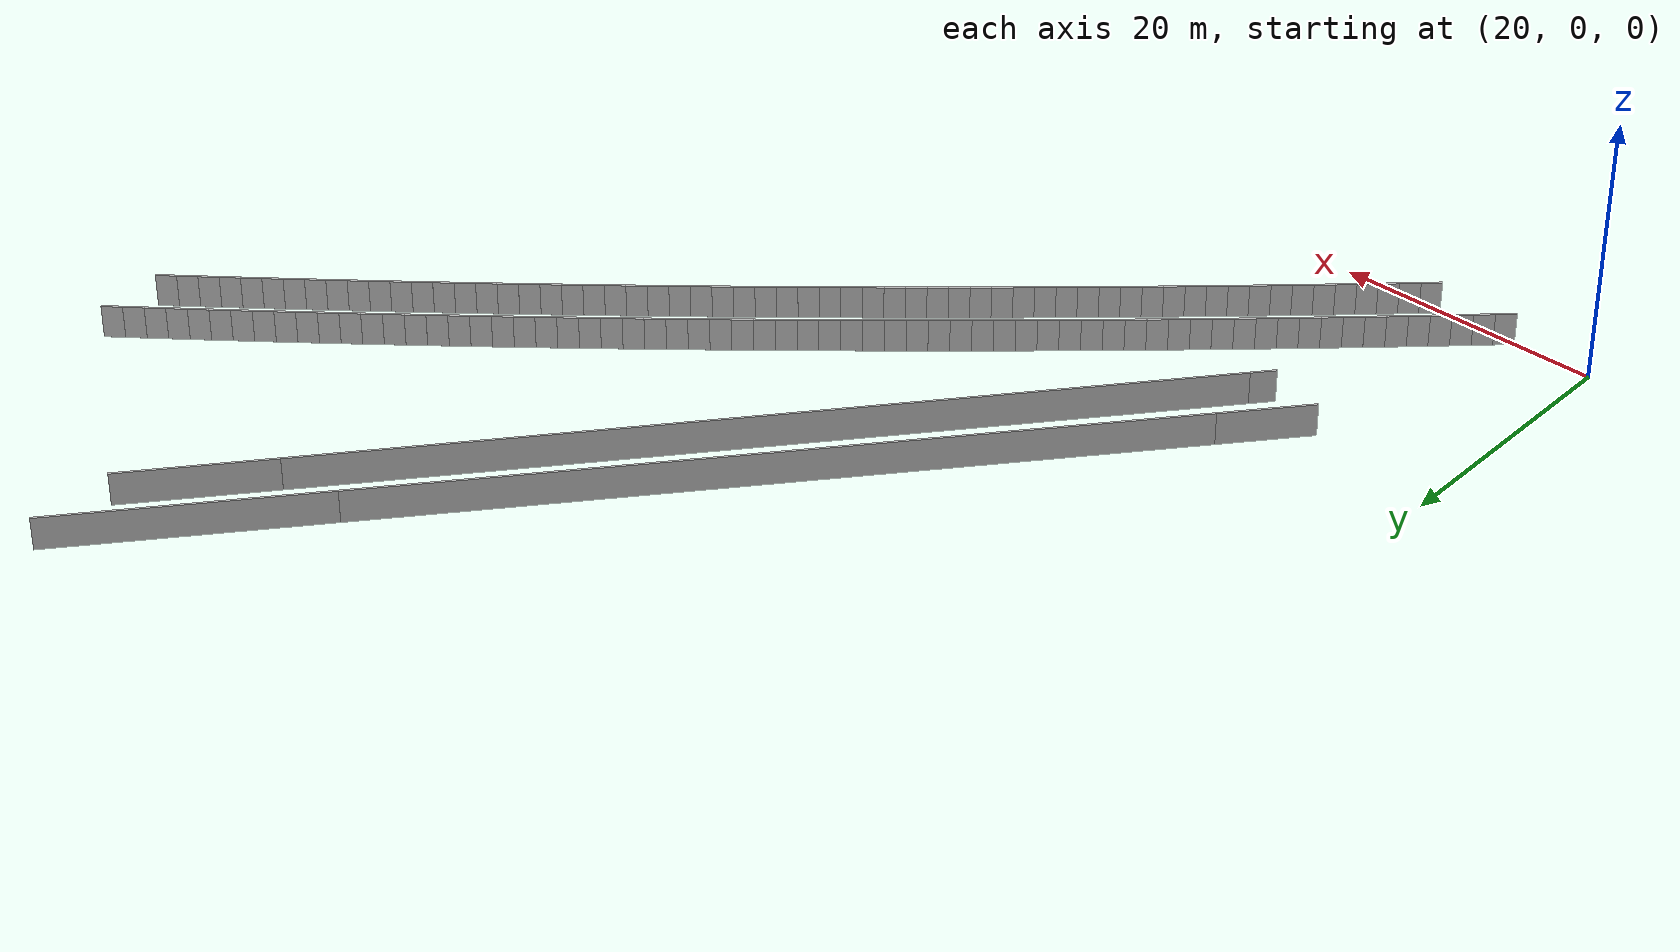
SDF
<?xml version="1.0" ?>
<sdf version="1.6">
  <model name="sps_0521">
    <pose frame="">0 0 0 0 -0 0</pose>
    <static>1</static>
    <self_collide>0</self_collide>
    <allow_auto_disable>0</allow_auto_disable>
    <link name="Wall213">
      <kinematic>0</kinematic>
      <gravity>1</gravity>
      <self_collide>0</self_collide>
      <collision name="collision">
        <geometry>
          <box>
            <size>19.7398 0.15 2.5</size>
          </box>
        </geometry>
        <pose frame="">0 0 0 0 -0 0</pose>
      </collision>
      <visual name="visual">
        <geometry>
          <box>
            <size>19.7398 0.15 2.5</size>
          </box>
        </geometry>
        <pose frame="">0 0 0 0 -0 0</pose>
        <cast_shadows>1</cast_shadows>
        <transparency>0.0</transparency>
      </visual>
      <pose frame="">78.1377 75.4643 1.25 0 0 -2.26727</pose>
    </link>
    <link name="Wall214">
      <kinematic>0</kinematic>
      <gravity>1</gravity>
      <self_collide>0</self_collide>
      <collision name="collision">
        <geometry>
          <box>
            <size>58.2001 0.15 2.5</size>
          </box>
        </geometry>
        <pose frame="">0 0 0 0 -0 0</pose>
      </collision>
      <visual name="visual">
        <geometry>
          <box>
            <size>58.2001 0.15 2.5</size>
          </box>
        </geometry>
        <pose frame="">0 0 0 0 -0 0</pose>
        <cast_shadows>1</cast_shadows>
        <transparency>0.0</transparency>
      </visual>
      <pose frame="">53.1377 45.5702 1.25 0 0 -2.26727</pose>
    </link>
    <link name="Wall215">
      <kinematic>0</kinematic>
      <gravity>1</gravity>
      <self_collide>0</self_collide>
      <collision name="collision">
        <geometry>
          <box>
            <size>6.97983 0.15 2.5</size>
          </box>
        </geometry>
        <pose frame="">0 0 0 0 -0 0</pose>
      </collision>
      <visual name="visual">
        <geometry>
          <box>
            <size>6.97983 0.15 2.5</size>
          </box>
        </geometry>
        <pose frame="">0 0 0 0 -0 0</pose>
        <cast_shadows>1</cast_shadows>
        <transparency>0.0</transparency>
      </visual>
      <pose frame="">32.2306 20.5702 1.25 0 0 -2.26727</pose>
    </link>
    <link name="Wall219">
      <kinematic>0</kinematic>
      <gravity>1</gravity>
      <self_collide>0</self_collide>
      <collision name="collision">
        <geometry>
          <box>
            <size>1.88109 0.15 2.5</size>
          </box>
        </geometry>
        <pose frame="">0 0 0 0 -0 0</pose>
      </collision>
      <visual name="visual">
        <geometry>
          <box>
            <size>1.88109 0.15 2.5</size>
          </box>
        </geometry>
        <pose frame="">0 0 0 0 -0 0</pose>
        <cast_shadows>1</cast_shadows>
        <transparency>0.0</transparency>
      </visual>
      <pose frame="">35.0712 17.1703 1.25 0 -0 0.876505</pose>
    </link>
    <link name="Wall220">
      <kinematic>0</kinematic>
      <gravity>1</gravity>
      <self_collide>0</self_collide>
      <collision name="collision">
        <geometry>
          <box>
            <size>65.0612 0.15 2.5</size>
          </box>
        </geometry>
        <pose frame="">0 0 0 0 -0 0</pose>
      </collision>
      <visual name="visual">
        <geometry>
          <box>
            <size>65.0612 0.15 2.5</size>
          </box>
        </geometry>
        <pose frame="">0 0 0 0 -0 0</pose>
        <cast_shadows>1</cast_shadows>
        <transparency>0.0</transparency>
      </visual>
      <pose frame="">56.4874 42.8931 1.25 0 -0 0.876505</pose>
    </link>
    <link name="Wall221">
      <kinematic>0</kinematic>
      <gravity>1</gravity>
      <self_collide>0</self_collide>
      <collision name="collision">
        <geometry>
          <box>
            <size>11.2021 0.15 2.5</size>
          </box>
        </geometry>
        <pose frame="">0 0 0 0 -0 0</pose>
      </collision>
      <visual name="visual">
        <geometry>
          <box>
            <size>11.2021 0.15 2.5</size>
          </box>
        </geometry>
        <pose frame="">0 0 0 0 -0 0</pose>
        <cast_shadows>1</cast_shadows>
        <transparency>0.0</transparency>
      </visual>
      <pose frame="">80.8857 72.1975 1.25 0 -0 0.876505</pose>
    </link>
    <link name="Wall3323">
      <kinematic>0</kinematic>
      <gravity>1</gravity>
      <self_collide>0</self_collide>
      <collision name="collision">
        <geometry>
          <box>
            <size>1.49661 0.15 2.5</size>
          </box>
        </geometry>
        <pose frame="">0 0 0 0 -0 0</pose>
      </collision>
      <visual name="visual">
        <geometry>
          <box>
            <size>1.49661 0.15 2.5</size>
          </box>
        </geometry>
        <pose frame="">0 0 0 0 -0 0</pose>
        <cast_shadows>1</cast_shadows>
        <transparency>0.0</transparency>
      </visual>
      <pose frame="">99.7113 58.1817 1.25 0 0 -2.47688</pose>
    </link>
    <link name="Wall3324">
      <kinematic>0</kinematic>
      <gravity>1</gravity>
      <self_collide>0</self_collide>
      <collision name="collision">
        <geometry>
          <box>
            <size>1.4965 0.15 2.5</size>
          </box>
        </geometry>
        <pose frame="">0 0 0 0 -0 0</pose>
      </collision>
      <visual name="visual">
        <geometry>
          <box>
            <size>1.4965 0.15 2.5</size>
          </box>
        </geometry>
        <pose frame="">0 0 0 0 -0 0</pose>
        <cast_shadows>1</cast_shadows>
        <transparency>0.0</transparency>
      </visual>
      <pose frame="">98.5341 57.2576 1.25 0 0 -2.47527</pose>
    </link>
    <link name="Wall3325">
      <kinematic>0</kinematic>
      <gravity>1</gravity>
      <self_collide>0</self_collide>
      <collision name="collision">
        <geometry>
          <box>
            <size>1.49638 0.15 2.5</size>
          </box>
        </geometry>
        <pose frame="">0 0 0 0 -0 0</pose>
      </collision>
      <visual name="visual">
        <geometry>
          <box>
            <size>1.49638 0.15 2.5</size>
          </box>
        </geometry>
        <pose frame="">0 0 0 0 -0 0</pose>
        <cast_shadows>1</cast_shadows>
        <transparency>0.0</transparency>
      </visual>
      <pose frame="">97.3585 56.3317 1.25 0 0 -2.47365</pose>
    </link>
    <link name="Wall3326">
      <kinematic>0</kinematic>
      <gravity>1</gravity>
      <self_collide>0</self_collide>
      <collision name="collision">
        <geometry>
          <box>
            <size>1.49672 0.15 2.5</size>
          </box>
        </geometry>
        <pose frame="">0 0 0 0 -0 0</pose>
      </collision>
      <visual name="visual">
        <geometry>
          <box>
            <size>1.49672 0.15 2.5</size>
          </box>
        </geometry>
        <pose frame="">0 0 0 0 -0 0</pose>
        <cast_shadows>1</cast_shadows>
        <transparency>0.0</transparency>
      </visual>
      <pose frame="">96.1843 55.4039 1.25 0 0 -2.47211</pose>
    </link>
    <link name="Wall3327">
      <kinematic>0</kinematic>
      <gravity>1</gravity>
      <self_collide>0</self_collide>
      <collision name="collision">
        <geometry>
          <box>
            <size>1.49653 0.15 2.5</size>
          </box>
        </geometry>
        <pose frame="">0 0 0 0 -0 0</pose>
      </collision>
      <visual name="visual">
        <geometry>
          <box>
            <size>1.49653 0.15 2.5</size>
          </box>
        </geometry>
        <pose frame="">0 0 0 0 -0 0</pose>
        <cast_shadows>1</cast_shadows>
        <transparency>0.0</transparency>
      </visual>
      <pose frame="">95.0114 54.4742 1.25 0 0 -2.4705</pose>
    </link>
    <link name="Wall3328">
      <kinematic>0</kinematic>
      <gravity>1</gravity>
      <self_collide>0</self_collide>
      <collision name="collision">
        <geometry>
          <box>
            <size>1.49639 0.15 2.5</size>
          </box>
        </geometry>
        <pose frame="">0 0 0 0 -0 0</pose>
      </collision>
      <visual name="visual">
        <geometry>
          <box>
            <size>1.49639 0.15 2.5</size>
          </box>
        </geometry>
        <pose frame="">0 0 0 0 -0 0</pose>
        <cast_shadows>1</cast_shadows>
        <transparency>0.0</transparency>
      </visual>
      <pose frame="">93.8402 53.5427 1.25 0 0 -2.46892</pose>
    </link>
    <link name="Wall3329">
      <kinematic>0</kinematic>
      <gravity>1</gravity>
      <self_collide>0</self_collide>
      <collision name="collision">
        <geometry>
          <box>
            <size>1.4965 0.15 2.5</size>
          </box>
        </geometry>
        <pose frame="">0 0 0 0 -0 0</pose>
      </collision>
      <visual name="visual">
        <geometry>
          <box>
            <size>1.4965 0.15 2.5</size>
          </box>
        </geometry>
        <pose frame="">0 0 0 0 -0 0</pose>
        <cast_shadows>1</cast_shadows>
        <transparency>0.0</transparency>
      </visual>
      <pose frame="">92.6706 52.6093 1.25 0 0 -2.46725</pose>
    </link>
    <link name="Wall3330">
      <kinematic>0</kinematic>
      <gravity>1</gravity>
      <self_collide>0</self_collide>
      <collision name="collision">
        <geometry>
          <box>
            <size>1.4966 0.15 2.5</size>
          </box>
        </geometry>
        <pose frame="">0 0 0 0 -0 0</pose>
      </collision>
      <visual name="visual">
        <geometry>
          <box>
            <size>1.4966 0.15 2.5</size>
          </box>
        </geometry>
        <pose frame="">0 0 0 0 -0 0</pose>
        <cast_shadows>1</cast_shadows>
        <transparency>0.0</transparency>
      </visual>
      <pose frame="">91.5023 51.674 1.25 0 0 -2.46574</pose>
    </link>
    <link name="Wall3331">
      <kinematic>0</kinematic>
      <gravity>1</gravity>
      <self_collide>0</self_collide>
      <collision name="collision">
        <geometry>
          <box>
            <size>1.49647 0.15 2.5</size>
          </box>
        </geometry>
        <pose frame="">0 0 0 0 -0 0</pose>
      </collision>
      <visual name="visual">
        <geometry>
          <box>
            <size>1.49647 0.15 2.5</size>
          </box>
        </geometry>
        <pose frame="">0 0 0 0 -0 0</pose>
        <cast_shadows>1</cast_shadows>
        <transparency>0.0</transparency>
      </visual>
      <pose frame="">90.3355 50.7369 1.25 0 0 -2.46415</pose>
    </link>
    <link name="Wall3332">
      <kinematic>0</kinematic>
      <gravity>1</gravity>
      <self_collide>0</self_collide>
      <collision name="collision">
        <geometry>
          <box>
            <size>1.49638 0.15 2.5</size>
          </box>
        </geometry>
        <pose frame="">0 0 0 0 -0 0</pose>
      </collision>
      <visual name="visual">
        <geometry>
          <box>
            <size>1.49638 0.15 2.5</size>
          </box>
        </geometry>
        <pose frame="">0 0 0 0 -0 0</pose>
        <cast_shadows>1</cast_shadows>
        <transparency>0.0</transparency>
      </visual>
      <pose frame="">89.1702 49.798 1.25 0 0 -2.46253</pose>
    </link>
    <link name="Wall3333">
      <kinematic>0</kinematic>
      <gravity>1</gravity>
      <self_collide>0</self_collide>
      <collision name="collision">
        <geometry>
          <box>
            <size>1.49654 0.15 2.5</size>
          </box>
        </geometry>
        <pose frame="">0 0 0 0 -0 0</pose>
      </collision>
      <visual name="visual">
        <geometry>
          <box>
            <size>1.49654 0.15 2.5</size>
          </box>
        </geometry>
        <pose frame="">0 0 0 0 -0 0</pose>
        <cast_shadows>1</cast_shadows>
        <transparency>0.0</transparency>
      </visual>
      <pose frame="">88.0064 48.8573 1.25 0 0 -2.4611</pose>
    </link>
    <link name="Wall3334">
      <kinematic>0</kinematic>
      <gravity>1</gravity>
      <self_collide>0</self_collide>
      <collision name="collision">
        <geometry>
          <box>
            <size>1.49653 0.15 2.5</size>
          </box>
        </geometry>
        <pose frame="">0 0 0 0 -0 0</pose>
      </collision>
      <visual name="visual">
        <geometry>
          <box>
            <size>1.49653 0.15 2.5</size>
          </box>
        </geometry>
        <pose frame="">0 0 0 0 -0 0</pose>
        <cast_shadows>1</cast_shadows>
        <transparency>0.0</transparency>
      </visual>
      <pose frame="">86.844 47.9147 1.25 0 0 -2.45936</pose>
    </link>
    <link name="Wall3335">
      <kinematic>0</kinematic>
      <gravity>1</gravity>
      <self_collide>0</self_collide>
      <collision name="collision">
        <geometry>
          <box>
            <size>1.49647 0.15 2.5</size>
          </box>
        </geometry>
        <pose frame="">0 0 0 0 -0 0</pose>
      </collision>
      <visual name="visual">
        <geometry>
          <box>
            <size>1.49647 0.15 2.5</size>
          </box>
        </geometry>
        <pose frame="">0 0 0 0 -0 0</pose>
        <cast_shadows>1</cast_shadows>
        <transparency>0.0</transparency>
      </visual>
      <pose frame="">85.6832 46.9702 1.25 0 0 -2.4578</pose>
    </link>
    <link name="Wall3336">
      <kinematic>0</kinematic>
      <gravity>1</gravity>
      <self_collide>0</self_collide>
      <collision name="collision">
        <geometry>
          <box>
            <size>1.49649 0.15 2.5</size>
          </box>
        </geometry>
        <pose frame="">0 0 0 0 -0 0</pose>
      </collision>
      <visual name="visual">
        <geometry>
          <box>
            <size>1.49649 0.15 2.5</size>
          </box>
        </geometry>
        <pose frame="">0 0 0 0 -0 0</pose>
        <cast_shadows>1</cast_shadows>
        <transparency>0.0</transparency>
      </visual>
      <pose frame="">84.5239 46.0239 1.25 0 0 -2.45623</pose>
    </link>
    <link name="Wall3337">
      <kinematic>0</kinematic>
      <gravity>1</gravity>
      <self_collide>0</self_collide>
      <collision name="collision">
        <geometry>
          <box>
            <size>1.49642 0.15 2.5</size>
          </box>
        </geometry>
        <pose frame="">0 0 0 0 -0 0</pose>
      </collision>
      <visual name="visual">
        <geometry>
          <box>
            <size>1.49642 0.15 2.5</size>
          </box>
        </geometry>
        <pose frame="">0 0 0 0 -0 0</pose>
        <cast_shadows>1</cast_shadows>
        <transparency>0.0</transparency>
      </visual>
      <pose frame="">83.3662 45.0758 1.25 0 0 -2.45461</pose>
    </link>
    <link name="Wall3338">
      <kinematic>0</kinematic>
      <gravity>1</gravity>
      <self_collide>0</self_collide>
      <collision name="collision">
        <geometry>
          <box>
            <size>1.49651 0.15 2.5</size>
          </box>
        </geometry>
        <pose frame="">0 0 0 0 -0 0</pose>
      </collision>
      <visual name="visual">
        <geometry>
          <box>
            <size>1.49651 0.15 2.5</size>
          </box>
        </geometry>
        <pose frame="">0 0 0 0 -0 0</pose>
        <cast_shadows>1</cast_shadows>
        <transparency>0.0</transparency>
      </visual>
      <pose frame="">82.2099 44.1259 1.25 0 0 -2.45313</pose>
    </link>
    <link name="Wall3339">
      <kinematic>0</kinematic>
      <gravity>1</gravity>
      <self_collide>0</self_collide>
      <collision name="collision">
        <geometry>
          <box>
            <size>1.49648 0.15 2.5</size>
          </box>
        </geometry>
        <pose frame="">0 0 0 0 -0 0</pose>
      </collision>
      <visual name="visual">
        <geometry>
          <box>
            <size>1.49648 0.15 2.5</size>
          </box>
        </geometry>
        <pose frame="">0 0 0 0 -0 0</pose>
        <cast_shadows>1</cast_shadows>
        <transparency>0.0</transparency>
      </visual>
      <pose frame="">81.055 43.1741 1.25 0 0 -2.45142</pose>
    </link>
    <link name="Wall3340">
      <kinematic>0</kinematic>
      <gravity>1</gravity>
      <self_collide>0</self_collide>
      <collision name="collision">
        <geometry>
          <box>
            <size>1.49656 0.15 2.5</size>
          </box>
        </geometry>
        <pose frame="">0 0 0 0 -0 0</pose>
      </collision>
      <visual name="visual">
        <geometry>
          <box>
            <size>1.49656 0.15 2.5</size>
          </box>
        </geometry>
        <pose frame="">0 0 0 0 -0 0</pose>
        <cast_shadows>1</cast_shadows>
        <transparency>0.0</transparency>
      </visual>
      <pose frame="">79.9018 42.2204 1.25 0 0 -2.44988</pose>
    </link>
    <link name="Wall3341">
      <kinematic>0</kinematic>
      <gravity>1</gravity>
      <self_collide>0</self_collide>
      <collision name="collision">
        <geometry>
          <box>
            <size>1.49653 0.15 2.5</size>
          </box>
        </geometry>
        <pose frame="">0 0 0 0 -0 0</pose>
      </collision>
      <visual name="visual">
        <geometry>
          <box>
            <size>1.49653 0.15 2.5</size>
          </box>
        </geometry>
        <pose frame="">0 0 0 0 -0 0</pose>
        <cast_shadows>1</cast_shadows>
        <transparency>0.0</transparency>
      </visual>
      <pose frame="">78.7499 41.265 1.25 0 0 -2.44844</pose>
    </link>
    <link name="Wall3342">
      <kinematic>0</kinematic>
      <gravity>1</gravity>
      <self_collide>0</self_collide>
      <collision name="collision">
        <geometry>
          <box>
            <size>1.49617 0.15 2.5</size>
          </box>
        </geometry>
        <pose frame="">0 0 0 0 -0 0</pose>
      </collision>
      <visual name="visual">
        <geometry>
          <box>
            <size>1.49617 0.15 2.5</size>
          </box>
        </geometry>
        <pose frame="">0 0 0 0 -0 0</pose>
        <cast_shadows>1</cast_shadows>
        <transparency>0.0</transparency>
      </visual>
      <pose frame="">77.5995 40.3081 1.25 0 0 -2.44707</pose>
    </link>
    <link name="Wall3343">
      <kinematic>0</kinematic>
      <gravity>1</gravity>
      <self_collide>0</self_collide>
      <collision name="collision">
        <geometry>
          <box>
            <size>1.4965 0.15 2.5</size>
          </box>
        </geometry>
        <pose frame="">0 0 0 0 -0 0</pose>
      </collision>
      <visual name="visual">
        <geometry>
          <box>
            <size>1.4965 0.15 2.5</size>
          </box>
        </geometry>
        <pose frame="">0 0 0 0 -0 0</pose>
        <cast_shadows>1</cast_shadows>
        <transparency>0.0</transparency>
      </visual>
      <pose frame="">76.4508 39.3492 1.25 0 0 -2.44496</pose>
    </link>
    <link name="Wall3344">
      <kinematic>0</kinematic>
      <gravity>1</gravity>
      <self_collide>0</self_collide>
      <collision name="collision">
        <geometry>
          <box>
            <size>1.49644 0.15 2.5</size>
          </box>
        </geometry>
        <pose frame="">0 0 0 0 -0 0</pose>
      </collision>
      <visual name="visual">
        <geometry>
          <box>
            <size>1.49644 0.15 2.5</size>
          </box>
        </geometry>
        <pose frame="">0 0 0 0 -0 0</pose>
        <cast_shadows>1</cast_shadows>
        <transparency>0.0</transparency>
      </visual>
      <pose frame="">75.3036 38.3882 1.25 0 0 -2.44355</pose>
    </link>
    <link name="Wall3345">
      <kinematic>0</kinematic>
      <gravity>1</gravity>
      <self_collide>0</self_collide>
      <collision name="collision">
        <geometry>
          <box>
            <size>1.4965 0.15 2.5</size>
          </box>
        </geometry>
        <pose frame="">0 0 0 0 -0 0</pose>
      </collision>
      <visual name="visual">
        <geometry>
          <box>
            <size>1.4965 0.15 2.5</size>
          </box>
        </geometry>
        <pose frame="">0 0 0 0 -0 0</pose>
        <cast_shadows>1</cast_shadows>
        <transparency>0.0</transparency>
      </visual>
      <pose frame="">74.158 37.4255 1.25 0 0 -2.44198</pose>
    </link>
    <link name="Wall3346">
      <kinematic>0</kinematic>
      <gravity>1</gravity>
      <self_collide>0</self_collide>
      <collision name="collision">
        <geometry>
          <box>
            <size>1.49659 0.15 2.5</size>
          </box>
        </geometry>
        <pose frame="">0 0 0 0 -0 0</pose>
      </collision>
      <visual name="visual">
        <geometry>
          <box>
            <size>1.49659 0.15 2.5</size>
          </box>
        </geometry>
        <pose frame="">0 0 0 0 -0 0</pose>
        <cast_shadows>1</cast_shadows>
        <transparency>0.0</transparency>
      </visual>
      <pose frame="">73.0138 36.4609 1.25 0 0 -2.44033</pose>
    </link>
    <link name="Wall3347">
      <kinematic>0</kinematic>
      <gravity>1</gravity>
      <self_collide>0</self_collide>
      <collision name="collision">
        <geometry>
          <box>
            <size>1.49653 0.15 2.5</size>
          </box>
        </geometry>
        <pose frame="">0 0 0 0 -0 0</pose>
      </collision>
      <visual name="visual">
        <geometry>
          <box>
            <size>1.49653 0.15 2.5</size>
          </box>
        </geometry>
        <pose frame="">0 0 0 0 -0 0</pose>
        <cast_shadows>1</cast_shadows>
        <transparency>0.0</transparency>
      </visual>
      <pose frame="">71.8711 35.4945 1.25 0 0 -2.43885</pose>
    </link>
    <link name="Wall3348">
      <kinematic>0</kinematic>
      <gravity>1</gravity>
      <self_collide>0</self_collide>
      <collision name="collision">
        <geometry>
          <box>
            <size>1.49652 0.15 2.5</size>
          </box>
        </geometry>
        <pose frame="">0 0 0 0 -0 0</pose>
      </collision>
      <visual name="visual">
        <geometry>
          <box>
            <size>1.49652 0.15 2.5</size>
          </box>
        </geometry>
        <pose frame="">0 0 0 0 -0 0</pose>
        <cast_shadows>1</cast_shadows>
        <transparency>0.0</transparency>
      </visual>
      <pose frame="">70.7299 34.5264 1.25 0 0 -2.43729</pose>
    </link>
    <link name="Wall3349">
      <kinematic>0</kinematic>
      <gravity>1</gravity>
      <self_collide>0</self_collide>
      <collision name="collision">
        <geometry>
          <box>
            <size>1.49657 0.15 2.5</size>
          </box>
        </geometry>
        <pose frame="">0 0 0 0 -0 0</pose>
      </collision>
      <visual name="visual">
        <geometry>
          <box>
            <size>1.49657 0.15 2.5</size>
          </box>
        </geometry>
        <pose frame="">0 0 0 0 -0 0</pose>
        <cast_shadows>1</cast_shadows>
        <transparency>0.0</transparency>
      </visual>
      <pose frame="">69.5902 33.5564 1.25 0 0 -2.43555</pose>
    </link>
    <link name="Wall3350">
      <kinematic>0</kinematic>
      <gravity>1</gravity>
      <self_collide>0</self_collide>
      <collision name="collision">
        <geometry>
          <box>
            <size>1.49639 0.15 2.5</size>
          </box>
        </geometry>
        <pose frame="">0 0 0 0 -0 0</pose>
      </collision>
      <visual name="visual">
        <geometry>
          <box>
            <size>1.49639 0.15 2.5</size>
          </box>
        </geometry>
        <pose frame="">0 0 0 0 -0 0</pose>
        <cast_shadows>1</cast_shadows>
        <transparency>0.0</transparency>
      </visual>
      <pose frame="">68.4522 32.5846 1.25 0 0 -2.43406</pose>
    </link>
    <link name="Wall3351">
      <kinematic>0</kinematic>
      <gravity>1</gravity>
      <self_collide>0</self_collide>
      <collision name="collision">
        <geometry>
          <box>
            <size>1.49659 0.15 2.5</size>
          </box>
        </geometry>
        <pose frame="">0 0 0 0 -0 0</pose>
      </collision>
      <visual name="visual">
        <geometry>
          <box>
            <size>1.49659 0.15 2.5</size>
          </box>
        </geometry>
        <pose frame="">0 0 0 0 -0 0</pose>
        <cast_shadows>1</cast_shadows>
        <transparency>0.0</transparency>
      </visual>
      <pose frame="">67.3158 31.611 1.25 0 0 -2.4324</pose>
    </link>
    <link name="Wall3352">
      <kinematic>0</kinematic>
      <gravity>1</gravity>
      <self_collide>0</self_collide>
      <collision name="collision">
        <geometry>
          <box>
            <size>1.49646 0.15 2.5</size>
          </box>
        </geometry>
        <pose frame="">0 0 0 0 -0 0</pose>
      </collision>
      <visual name="visual">
        <geometry>
          <box>
            <size>1.49646 0.15 2.5</size>
          </box>
        </geometry>
        <pose frame="">0 0 0 0 -0 0</pose>
        <cast_shadows>1</cast_shadows>
        <transparency>0.0</transparency>
      </visual>
      <pose frame="">66.1808 30.6356 1.25 0 0 -2.43093</pose>
    </link>
    <link name="Wall3353">
      <kinematic>0</kinematic>
      <gravity>1</gravity>
      <self_collide>0</self_collide>
      <collision name="collision">
        <geometry>
          <box>
            <size>1.49642 0.15 2.5</size>
          </box>
        </geometry>
        <pose frame="">0 0 0 0 -0 0</pose>
      </collision>
      <visual name="visual">
        <geometry>
          <box>
            <size>1.49642 0.15 2.5</size>
          </box>
        </geometry>
        <pose frame="">0 0 0 0 -0 0</pose>
        <cast_shadows>1</cast_shadows>
        <transparency>0.0</transparency>
      </visual>
      <pose frame="">65.0474 29.6585 1.25 0 0 -2.42934</pose>
    </link>
    <link name="Wall3354">
      <kinematic>0</kinematic>
      <gravity>1</gravity>
      <self_collide>0</self_collide>
      <collision name="collision">
        <geometry>
          <box>
            <size>1.49651 0.15 2.5</size>
          </box>
        </geometry>
        <pose frame="">0 0 0 0 -0 0</pose>
      </collision>
      <visual name="visual">
        <geometry>
          <box>
            <size>1.49651 0.15 2.5</size>
          </box>
        </geometry>
        <pose frame="">0 0 0 0 -0 0</pose>
        <cast_shadows>1</cast_shadows>
        <transparency>0.0</transparency>
      </visual>
      <pose frame="">63.9155 28.6796 1.25 0 0 -2.42778</pose>
    </link>
    <link name="Wall3355">
      <kinematic>0</kinematic>
      <gravity>1</gravity>
      <self_collide>0</self_collide>
      <collision name="collision">
        <geometry>
          <box>
            <size>1.49649 0.15 2.5</size>
          </box>
        </geometry>
        <pose frame="">0 0 0 0 -0 0</pose>
      </collision>
      <visual name="visual">
        <geometry>
          <box>
            <size>1.49649 0.15 2.5</size>
          </box>
        </geometry>
        <pose frame="">0 0 0 0 -0 0</pose>
        <cast_shadows>1</cast_shadows>
        <transparency>0.0</transparency>
      </visual>
      <pose frame="">62.7852 27.6988 1.25 0 0 -2.42599</pose>
    </link>
    <link name="Wall3356">
      <kinematic>0</kinematic>
      <gravity>1</gravity>
      <self_collide>0</self_collide>
      <collision name="collision">
        <geometry>
          <box>
            <size>1.49652 0.15 2.5</size>
          </box>
        </geometry>
        <pose frame="">0 0 0 0 -0 0</pose>
      </collision>
      <visual name="visual">
        <geometry>
          <box>
            <size>1.49652 0.15 2.5</size>
          </box>
        </geometry>
        <pose frame="">0 0 0 0 -0 0</pose>
        <cast_shadows>1</cast_shadows>
        <transparency>0.0</transparency>
      </visual>
      <pose frame="">61.6565 26.7162 1.25 0 0 -2.4246</pose>
    </link>
    <link name="Wall3357">
      <kinematic>0</kinematic>
      <gravity>1</gravity>
      <self_collide>0</self_collide>
      <collision name="collision">
        <geometry>
          <box>
            <size>1.49648 0.15 2.5</size>
          </box>
        </geometry>
        <pose frame="">0 0 0 0 -0 0</pose>
      </collision>
      <visual name="visual">
        <geometry>
          <box>
            <size>1.49648 0.15 2.5</size>
          </box>
        </geometry>
        <pose frame="">0 0 0 0 -0 0</pose>
        <cast_shadows>1</cast_shadows>
        <transparency>0.0</transparency>
      </visual>
      <pose frame="">60.5292 25.7319 1.25 0 0 -2.42295</pose>
    </link>
    <link name="Wall3358">
      <kinematic>0</kinematic>
      <gravity>1</gravity>
      <self_collide>0</self_collide>
      <collision name="collision">
        <geometry>
          <box>
            <size>1.49659 0.15 2.5</size>
          </box>
        </geometry>
        <pose frame="">0 0 0 0 -0 0</pose>
      </collision>
      <visual name="visual">
        <geometry>
          <box>
            <size>1.49659 0.15 2.5</size>
          </box>
        </geometry>
        <pose frame="">0 0 0 0 -0 0</pose>
        <cast_shadows>1</cast_shadows>
        <transparency>0.0</transparency>
      </visual>
      <pose frame="">59.4035 24.7458 1.25 0 0 -2.42144</pose>
    </link>
    <link name="Wall3359">
      <kinematic>0</kinematic>
      <gravity>1</gravity>
      <self_collide>0</self_collide>
      <collision name="collision">
        <geometry>
          <box>
            <size>1.49639 0.15 2.5</size>
          </box>
        </geometry>
        <pose frame="">0 0 0 0 -0 0</pose>
      </collision>
      <visual name="visual">
        <geometry>
          <box>
            <size>1.49639 0.15 2.5</size>
          </box>
        </geometry>
        <pose frame="">0 0 0 0 -0 0</pose>
        <cast_shadows>1</cast_shadows>
        <transparency>0.0</transparency>
      </visual>
      <pose frame="">58.2794 23.7579 1.25 0 0 -2.41975</pose>
    </link>
    <link name="Wall3360">
      <kinematic>0</kinematic>
      <gravity>1</gravity>
      <self_collide>0</self_collide>
      <collision name="collision">
        <geometry>
          <box>
            <size>1.49659 0.15 2.5</size>
          </box>
        </geometry>
        <pose frame="">0 0 0 0 -0 0</pose>
      </collision>
      <visual name="visual">
        <geometry>
          <box>
            <size>1.49659 0.15 2.5</size>
          </box>
        </geometry>
        <pose frame="">0 0 0 0 -0 0</pose>
        <cast_shadows>1</cast_shadows>
        <transparency>0.0</transparency>
      </visual>
      <pose frame="">57.1569 22.7682 1.25 0 0 -2.41824</pose>
    </link>
    <link name="Wall3361">
      <kinematic>0</kinematic>
      <gravity>1</gravity>
      <self_collide>0</self_collide>
      <collision name="collision">
        <geometry>
          <box>
            <size>1.49641 0.15 2.5</size>
          </box>
        </geometry>
        <pose frame="">0 0 0 0 -0 0</pose>
      </collision>
      <visual name="visual">
        <geometry>
          <box>
            <size>1.49641 0.15 2.5</size>
          </box>
        </geometry>
        <pose frame="">0 0 0 0 -0 0</pose>
        <cast_shadows>1</cast_shadows>
        <transparency>0.0</transparency>
      </visual>
      <pose frame="">56.0359 21.7768 1.25 0 0 -2.41671</pose>
    </link>
    <link name="Wall3362">
      <kinematic>0</kinematic>
      <gravity>1</gravity>
      <self_collide>0</self_collide>
      <collision name="collision">
        <geometry>
          <box>
            <size>1.49656 0.15 2.5</size>
          </box>
        </geometry>
        <pose frame="">0 0 0 0 -0 0</pose>
      </collision>
      <visual name="visual">
        <geometry>
          <box>
            <size>1.49656 0.15 2.5</size>
          </box>
        </geometry>
        <pose frame="">0 0 0 0 -0 0</pose>
        <cast_shadows>1</cast_shadows>
        <transparency>0.0</transparency>
      </visual>
      <pose frame="">54.9166 20.7836 1.25 0 0 -2.415</pose>
    </link>
    <link name="Wall3363">
      <kinematic>0</kinematic>
      <gravity>1</gravity>
      <self_collide>0</self_collide>
      <collision name="collision">
        <geometry>
          <box>
            <size>1.49647 0.15 2.5</size>
          </box>
        </geometry>
        <pose frame="">0 0 0 0 -0 0</pose>
      </collision>
      <visual name="visual">
        <geometry>
          <box>
            <size>1.49647 0.15 2.5</size>
          </box>
        </geometry>
        <pose frame="">0 0 0 0 -0 0</pose>
        <cast_shadows>1</cast_shadows>
        <transparency>0.0</transparency>
      </visual>
      <pose frame="">53.7988 19.7886 1.25 0 0 -2.41347</pose>
    </link>
    <link name="Wall3364">
      <kinematic>0</kinematic>
      <gravity>1</gravity>
      <self_collide>0</self_collide>
      <collision name="collision">
        <geometry>
          <box>
            <size>1.49654 0.15 2.5</size>
          </box>
        </geometry>
        <pose frame="">0 0 0 0 -0 0</pose>
      </collision>
      <visual name="visual">
        <geometry>
          <box>
            <size>1.49654 0.15 2.5</size>
          </box>
        </geometry>
        <pose frame="">0 0 0 0 -0 0</pose>
        <cast_shadows>1</cast_shadows>
        <transparency>0.0</transparency>
      </visual>
      <pose frame="">52.6825 18.7918 1.25 0 0 -2.41182</pose>
    </link>
    <link name="Wall3365">
      <kinematic>0</kinematic>
      <gravity>1</gravity>
      <self_collide>0</self_collide>
      <collision name="collision">
        <geometry>
          <box>
            <size>1.49646 0.15 2.5</size>
          </box>
        </geometry>
        <pose frame="">0 0 0 0 -0 0</pose>
      </collision>
      <visual name="visual">
        <geometry>
          <box>
            <size>1.49646 0.15 2.5</size>
          </box>
        </geometry>
        <pose frame="">0 0 0 0 -0 0</pose>
        <cast_shadows>1</cast_shadows>
        <transparency>0.0</transparency>
      </visual>
      <pose frame="">51.568 17.7932 1.25 0 0 -2.41024</pose>
    </link>
    <link name="Wall3366">
      <kinematic>0</kinematic>
      <gravity>1</gravity>
      <self_collide>0</self_collide>
      <collision name="collision">
        <geometry>
          <box>
            <size>1.49646 0.15 2.5</size>
          </box>
        </geometry>
        <pose frame="">0 0 0 0 -0 0</pose>
      </collision>
      <visual name="visual">
        <geometry>
          <box>
            <size>1.49646 0.15 2.5</size>
          </box>
        </geometry>
        <pose frame="">0 0 0 0 -0 0</pose>
        <cast_shadows>1</cast_shadows>
        <transparency>0.0</transparency>
      </visual>
      <pose frame="">50.4549 16.7929 1.25 0 0 -2.40871</pose>
    </link>
    <link name="Wall3367">
      <kinematic>0</kinematic>
      <gravity>1</gravity>
      <self_collide>0</self_collide>
      <collision name="collision">
        <geometry>
          <box>
            <size>1.4966 0.15 2.5</size>
          </box>
        </geometry>
        <pose frame="">0 0 0 0 -0 0</pose>
      </collision>
      <visual name="visual">
        <geometry>
          <box>
            <size>1.4966 0.15 2.5</size>
          </box>
        </geometry>
        <pose frame="">0 0 0 0 -0 0</pose>
        <cast_shadows>1</cast_shadows>
        <transparency>0.0</transparency>
      </visual>
      <pose frame="">49.3434 15.7908 1.25 0 0 -2.40714</pose>
    </link>
    <link name="Wall3368">
      <kinematic>0</kinematic>
      <gravity>1</gravity>
      <self_collide>0</self_collide>
      <collision name="collision">
        <geometry>
          <box>
            <size>1.4964 0.15 2.5</size>
          </box>
        </geometry>
        <pose frame="">0 0 0 0 -0 0</pose>
      </collision>
      <visual name="visual">
        <geometry>
          <box>
            <size>1.4964 0.15 2.5</size>
          </box>
        </geometry>
        <pose frame="">0 0 0 0 -0 0</pose>
        <cast_shadows>1</cast_shadows>
        <transparency>0.0</transparency>
      </visual>
      <pose frame="">48.2335 14.787 1.25 0 0 -2.40553</pose>
    </link>
    <link name="Wall3369">
      <kinematic>0</kinematic>
      <gravity>1</gravity>
      <self_collide>0</self_collide>
      <collision name="collision">
        <geometry>
          <box>
            <size>1.49667 0.15 2.5</size>
          </box>
        </geometry>
        <pose frame="">0 0 0 0 -0 0</pose>
      </collision>
      <visual name="visual">
        <geometry>
          <box>
            <size>1.49667 0.15 2.5</size>
          </box>
        </geometry>
        <pose frame="">0 0 0 0 -0 0</pose>
        <cast_shadows>1</cast_shadows>
        <transparency>0.0</transparency>
      </visual>
      <pose frame="">47.1252 13.7814 1.25 0 0 -2.40394</pose>
    </link>
    <link name="Wall3370">
      <kinematic>0</kinematic>
      <gravity>1</gravity>
      <self_collide>0</self_collide>
      <collision name="collision">
        <geometry>
          <box>
            <size>1.49638 0.15 2.5</size>
          </box>
        </geometry>
        <pose frame="">0 0 0 0 -0 0</pose>
      </collision>
      <visual name="visual">
        <geometry>
          <box>
            <size>1.49638 0.15 2.5</size>
          </box>
        </geometry>
        <pose frame="">0 0 0 0 -0 0</pose>
        <cast_shadows>1</cast_shadows>
        <transparency>0.0</transparency>
      </visual>
      <pose frame="">46.0185 12.774 1.25 0 0 -2.40233</pose>
    </link>
    <link name="Wall3371">
      <kinematic>0</kinematic>
      <gravity>1</gravity>
      <self_collide>0</self_collide>
      <collision name="collision">
        <geometry>
          <box>
            <size>1.49663 0.15 2.5</size>
          </box>
        </geometry>
        <pose frame="">0 0 0 0 -0 0</pose>
      </collision>
      <visual name="visual">
        <geometry>
          <box>
            <size>1.49663 0.15 2.5</size>
          </box>
        </geometry>
        <pose frame="">0 0 0 0 -0 0</pose>
        <cast_shadows>1</cast_shadows>
        <transparency>0.0</transparency>
      </visual>
      <pose frame="">44.9134 11.7649 1.25 0 0 -2.40082</pose>
    </link>
    <link name="Wall3372">
      <kinematic>0</kinematic>
      <gravity>1</gravity>
      <self_collide>0</self_collide>
      <collision name="collision">
        <geometry>
          <box>
            <size>1.49635 0.15 2.5</size>
          </box>
        </geometry>
        <pose frame="">0 0 0 0 -0 0</pose>
      </collision>
      <visual name="visual">
        <geometry>
          <box>
            <size>1.49635 0.15 2.5</size>
          </box>
        </geometry>
        <pose frame="">0 0 0 0 -0 0</pose>
        <cast_shadows>1</cast_shadows>
        <transparency>0.0</transparency>
      </visual>
      <pose frame="">43.8099 10.7541 1.25 0 0 -2.39921</pose>
    </link>
    <link name="Wall3373">
      <kinematic>0</kinematic>
      <gravity>1</gravity>
      <self_collide>0</self_collide>
      <collision name="collision">
        <geometry>
          <box>
            <size>1.49655 0.15 2.5</size>
          </box>
        </geometry>
        <pose frame="">0 0 0 0 -0 0</pose>
      </collision>
      <visual name="visual">
        <geometry>
          <box>
            <size>1.49655 0.15 2.5</size>
          </box>
        </geometry>
        <pose frame="">0 0 0 0 -0 0</pose>
        <cast_shadows>1</cast_shadows>
        <transparency>0.0</transparency>
      </visual>
      <pose frame="">42.708 9.74159 1.25 0 0 -2.39768</pose>
    </link>
    <link name="Wall3374">
      <kinematic>0</kinematic>
      <gravity>1</gravity>
      <self_collide>0</self_collide>
      <collision name="collision">
        <geometry>
          <box>
            <size>1.49641 0.15 2.5</size>
          </box>
        </geometry>
        <pose frame="">0 0 0 0 -0 0</pose>
      </collision>
      <visual name="visual">
        <geometry>
          <box>
            <size>1.49641 0.15 2.5</size>
          </box>
        </geometry>
        <pose frame="">0 0 0 0 -0 0</pose>
        <cast_shadows>1</cast_shadows>
        <transparency>0.0</transparency>
      </visual>
      <pose frame="">41.6077 8.72728 1.25 0 0 -2.39598</pose>
    </link>
    <link name="Wall3375">
      <kinematic>0</kinematic>
      <gravity>1</gravity>
      <self_collide>0</self_collide>
      <collision name="collision">
        <geometry>
          <box>
            <size>1.49621 0.15 2.5</size>
          </box>
        </geometry>
        <pose frame="">0 0 0 0 -0 0</pose>
      </collision>
      <visual name="visual">
        <geometry>
          <box>
            <size>1.49621 0.15 2.5</size>
          </box>
        </geometry>
        <pose frame="">0 0 0 0 -0 0</pose>
        <cast_shadows>1</cast_shadows>
        <transparency>0.0</transparency>
      </visual>
      <pose frame="">40.5091 7.7115 1.25 0 0 -2.3948</pose>
    </link>
    <link name="Wall3376">
      <kinematic>0</kinematic>
      <gravity>1</gravity>
      <self_collide>0</self_collide>
      <collision name="collision">
        <geometry>
          <box>
            <size>1.4964 0.15 2.5</size>
          </box>
        </geometry>
        <pose frame="">0 0 0 0 -0 0</pose>
      </collision>
      <visual name="visual">
        <geometry>
          <box>
            <size>1.4964 0.15 2.5</size>
          </box>
        </geometry>
        <pose frame="">0 0 0 0 -0 0</pose>
        <cast_shadows>1</cast_shadows>
        <transparency>0.0</transparency>
      </visual>
      <pose frame="">39.4119 6.69401 1.25 0 0 -2.39286</pose>
    </link>
    <link name="Wall3377">
      <kinematic>0</kinematic>
      <gravity>1</gravity>
      <self_collide>0</self_collide>
      <collision name="collision">
        <geometry>
          <box>
            <size>1.49674 0.15 2.5</size>
          </box>
        </geometry>
        <pose frame="">0 0 0 0 -0 0</pose>
      </collision>
      <visual name="visual">
        <geometry>
          <box>
            <size>1.49674 0.15 2.5</size>
          </box>
        </geometry>
        <pose frame="">0 0 0 0 -0 0</pose>
        <cast_shadows>1</cast_shadows>
        <transparency>0.0</transparency>
      </visual>
      <pose frame="">38.3165 5.67439 1.25 0 0 -2.39124</pose>
    </link>
    <link name="Wall3378">
      <kinematic>0</kinematic>
      <gravity>1</gravity>
      <self_collide>0</self_collide>
      <collision name="collision">
        <geometry>
          <box>
            <size>1.49637 0.15 2.5</size>
          </box>
        </geometry>
        <pose frame="">0 0 0 0 -0 0</pose>
      </collision>
      <visual name="visual">
        <geometry>
          <box>
            <size>1.49637 0.15 2.5</size>
          </box>
        </geometry>
        <pose frame="">0 0 0 0 -0 0</pose>
        <cast_shadows>1</cast_shadows>
        <transparency>0.0</transparency>
      </visual>
      <pose frame="">37.2226 4.65309 1.25 0 0 -2.38977</pose>
    </link>
    <link name="Wall3379">
      <kinematic>0</kinematic>
      <gravity>1</gravity>
      <self_collide>0</self_collide>
      <collision name="collision">
        <geometry>
          <box>
            <size>1.49654 0.15 2.5</size>
          </box>
        </geometry>
        <pose frame="">0 0 0 0 -0 0</pose>
      </collision>
      <visual name="visual">
        <geometry>
          <box>
            <size>1.49654 0.15 2.5</size>
          </box>
        </geometry>
        <pose frame="">0 0 0 0 -0 0</pose>
        <cast_shadows>1</cast_shadows>
        <transparency>0.0</transparency>
      </visual>
      <pose frame="">36.1304 3.63011 1.25 0 0 -2.38804</pose>
    </link>
    <link name="Wall3380">
      <kinematic>0</kinematic>
      <gravity>1</gravity>
      <self_collide>0</self_collide>
      <collision name="collision">
        <geometry>
          <box>
            <size>1.49643 0.15 2.5</size>
          </box>
        </geometry>
        <pose frame="">0 0 0 0 -0 0</pose>
      </collision>
      <visual name="visual">
        <geometry>
          <box>
            <size>1.49643 0.15 2.5</size>
          </box>
        </geometry>
        <pose frame="">0 0 0 0 -0 0</pose>
        <cast_shadows>1</cast_shadows>
        <transparency>0.0</transparency>
      </visual>
      <pose frame="">35.0398 2.60539 1.25 0 0 -2.38663</pose>
    </link>
    <link name="Wall3381">
      <kinematic>0</kinematic>
      <gravity>1</gravity>
      <self_collide>0</self_collide>
      <collision name="collision">
        <geometry>
          <box>
            <size>1.49635 0.15 2.5</size>
          </box>
        </geometry>
        <pose frame="">0 0 0 0 -0 0</pose>
      </collision>
      <visual name="visual">
        <geometry>
          <box>
            <size>1.49635 0.15 2.5</size>
          </box>
        </geometry>
        <pose frame="">0 0 0 0 -0 0</pose>
        <cast_shadows>1</cast_shadows>
        <transparency>0.0</transparency>
      </visual>
      <pose frame="">33.9509 1.57899 1.25 0 0 -2.38484</pose>
    </link>
    <link name="Wall3382">
      <kinematic>0</kinematic>
      <gravity>1</gravity>
      <self_collide>0</self_collide>
      <collision name="collision">
        <geometry>
          <box>
            <size>1.49638 0.15 2.5</size>
          </box>
        </geometry>
        <pose frame="">0 0 0 0 -0 0</pose>
      </collision>
      <visual name="visual">
        <geometry>
          <box>
            <size>1.49638 0.15 2.5</size>
          </box>
        </geometry>
        <pose frame="">0 0 0 0 -0 0</pose>
        <cast_shadows>1</cast_shadows>
        <transparency>0.0</transparency>
      </visual>
      <pose frame="">32.8636 0.550918 1.25 0 0 -2.38351</pose>
    </link>
    <link name="Wall5932">
      <kinematic>0</kinematic>
      <gravity>1</gravity>
      <self_collide>0</self_collide>
      <collision name="collision">
        <geometry>
          <box>
            <size>1.50311 0.15 2.5</size>
          </box>
        </geometry>
        <pose frame="">0 0 0 0 -0 0</pose>
      </collision>
      <visual name="visual">
        <geometry>
          <box>
            <size>1.50311 0.15 2.5</size>
          </box>
        </geometry>
        <pose frame="">0 0 0 0 -0 0</pose>
        <cast_shadows>1</cast_shadows>
        <transparency>0.0</transparency>
      </visual>
      <pose frame="">99.5163 63.283 1.25 0 0 -2.48006</pose>
    </link>
    <link name="Wall5933">
      <kinematic>0</kinematic>
      <gravity>1</gravity>
      <self_collide>0</self_collide>
      <collision name="collision">
        <geometry>
          <box>
            <size>1.50305 0.15 2.5</size>
          </box>
        </geometry>
        <pose frame="">0 0 0 0 -0 0</pose>
      </collision>
      <visual name="visual">
        <geometry>
          <box>
            <size>1.50305 0.15 2.5</size>
          </box>
        </geometry>
        <pose frame="">0 0 0 0 -0 0</pose>
        <cast_shadows>1</cast_shadows>
        <transparency>0.0</transparency>
      </visual>
      <pose frame="">98.331 62.3586 1.25 0 0 -2.47833</pose>
    </link>
    <link name="Wall5934">
      <kinematic>0</kinematic>
      <gravity>1</gravity>
      <self_collide>0</self_collide>
      <collision name="collision">
        <geometry>
          <box>
            <size>1.50315 0.15 2.5</size>
          </box>
        </geometry>
        <pose frame="">0 0 0 0 -0 0</pose>
      </collision>
      <visual name="visual">
        <geometry>
          <box>
            <size>1.50315 0.15 2.5</size>
          </box>
        </geometry>
        <pose frame="">0 0 0 0 -0 0</pose>
        <cast_shadows>1</cast_shadows>
        <transparency>0.0</transparency>
      </visual>
      <pose frame="">97.1474 61.4322 1.25 0 0 -2.47673</pose>
    </link>
    <link name="Wall5935">
      <kinematic>0</kinematic>
      <gravity>1</gravity>
      <self_collide>0</self_collide>
      <collision name="collision">
        <geometry>
          <box>
            <size>1.50323 0.15 2.5</size>
          </box>
        </geometry>
        <pose frame="">0 0 0 0 -0 0</pose>
      </collision>
      <visual name="visual">
        <geometry>
          <box>
            <size>1.50323 0.15 2.5</size>
          </box>
        </geometry>
        <pose frame="">0 0 0 0 -0 0</pose>
        <cast_shadows>1</cast_shadows>
        <transparency>0.0</transparency>
      </visual>
      <pose frame="">95.965 60.5039 1.25 0 0 -2.47522</pose>
    </link>
    <link name="Wall5936">
      <kinematic>0</kinematic>
      <gravity>1</gravity>
      <self_collide>0</self_collide>
      <collision name="collision">
        <geometry>
          <box>
            <size>1.50295 0.15 2.5</size>
          </box>
        </geometry>
        <pose frame="">0 0 0 0 -0 0</pose>
      </collision>
      <visual name="visual">
        <geometry>
          <box>
            <size>1.50295 0.15 2.5</size>
          </box>
        </geometry>
        <pose frame="">0 0 0 0 -0 0</pose>
        <cast_shadows>1</cast_shadows>
        <transparency>0.0</transparency>
      </visual>
      <pose frame="">94.7842 59.5739 1.25 0 0 -2.47368</pose>
    </link>
    <link name="Wall5937">
      <kinematic>0</kinematic>
      <gravity>1</gravity>
      <self_collide>0</self_collide>
      <collision name="collision">
        <geometry>
          <box>
            <size>1.5032 0.15 2.5</size>
          </box>
        </geometry>
        <pose frame="">0 0 0 0 -0 0</pose>
      </collision>
      <visual name="visual">
        <geometry>
          <box>
            <size>1.5032 0.15 2.5</size>
          </box>
        </geometry>
        <pose frame="">0 0 0 0 -0 0</pose>
        <cast_shadows>1</cast_shadows>
        <transparency>0.0</transparency>
      </visual>
      <pose frame="">93.6049 58.6421 1.25 0 0 -2.47216</pose>
    </link>
    <link name="Wall5938">
      <kinematic>0</kinematic>
      <gravity>1</gravity>
      <self_collide>0</self_collide>
      <collision name="collision">
        <geometry>
          <box>
            <size>1.50303 0.15 2.5</size>
          </box>
        </geometry>
        <pose frame="">0 0 0 0 -0 0</pose>
      </collision>
      <visual name="visual">
        <geometry>
          <box>
            <size>1.50303 0.15 2.5</size>
          </box>
        </geometry>
        <pose frame="">0 0 0 0 -0 0</pose>
        <cast_shadows>1</cast_shadows>
        <transparency>0.0</transparency>
      </visual>
      <pose frame="">92.427 57.7083 1.25 0 0 -2.47041</pose>
    </link>
    <link name="Wall5939">
      <kinematic>0</kinematic>
      <gravity>1</gravity>
      <self_collide>0</self_collide>
      <collision name="collision">
        <geometry>
          <box>
            <size>1.50311 0.15 2.5</size>
          </box>
        </geometry>
        <pose frame="">0 0 0 0 -0 0</pose>
      </collision>
      <visual name="visual">
        <geometry>
          <box>
            <size>1.50311 0.15 2.5</size>
          </box>
        </geometry>
        <pose frame="">0 0 0 0 -0 0</pose>
        <cast_shadows>1</cast_shadows>
        <transparency>0.0</transparency>
      </visual>
      <pose frame="">91.2507 56.7726 1.25 0 0 -2.46884</pose>
    </link>
    <link name="Wall5940">
      <kinematic>0</kinematic>
      <gravity>1</gravity>
      <self_collide>0</self_collide>
      <collision name="collision">
        <geometry>
          <box>
            <size>1.50293 0.15 2.5</size>
          </box>
        </geometry>
        <pose frame="">0 0 0 0 -0 0</pose>
      </collision>
      <visual name="visual">
        <geometry>
          <box>
            <size>1.50293 0.15 2.5</size>
          </box>
        </geometry>
        <pose frame="">0 0 0 0 -0 0</pose>
        <cast_shadows>1</cast_shadows>
        <transparency>0.0</transparency>
      </visual>
      <pose frame="">90.0759 55.8351 1.25 0 0 -2.4673</pose>
    </link>
    <link name="Wall5941">
      <kinematic>0</kinematic>
      <gravity>1</gravity>
      <self_collide>0</self_collide>
      <collision name="collision">
        <geometry>
          <box>
            <size>1.50302 0.15 2.5</size>
          </box>
        </geometry>
        <pose frame="">0 0 0 0 -0 0</pose>
      </collision>
      <visual name="visual">
        <geometry>
          <box>
            <size>1.50302 0.15 2.5</size>
          </box>
        </geometry>
        <pose frame="">0 0 0 0 -0 0</pose>
        <cast_shadows>1</cast_shadows>
        <transparency>0.0</transparency>
      </visual>
      <pose frame="">88.9025 54.8958 1.25 0 0 -2.46573</pose>
    </link>
    <link name="Wall5942">
      <kinematic>0</kinematic>
      <gravity>1</gravity>
      <self_collide>0</self_collide>
      <collision name="collision">
        <geometry>
          <box>
            <size>1.50315 0.15 2.5</size>
          </box>
        </geometry>
        <pose frame="">0 0 0 0 -0 0</pose>
      </collision>
      <visual name="visual">
        <geometry>
          <box>
            <size>1.50315 0.15 2.5</size>
          </box>
        </geometry>
        <pose frame="">0 0 0 0 -0 0</pose>
        <cast_shadows>1</cast_shadows>
        <transparency>0.0</transparency>
      </visual>
      <pose frame="">87.7306 53.9546 1.25 0 0 -2.46413</pose>
    </link>
    <link name="Wall5943">
      <kinematic>0</kinematic>
      <gravity>1</gravity>
      <self_collide>0</self_collide>
      <collision name="collision">
        <geometry>
          <box>
            <size>1.50317 0.15 2.5</size>
          </box>
        </geometry>
        <pose frame="">0 0 0 0 -0 0</pose>
      </collision>
      <visual name="visual">
        <geometry>
          <box>
            <size>1.50317 0.15 2.5</size>
          </box>
        </geometry>
        <pose frame="">0 0 0 0 -0 0</pose>
        <cast_shadows>1</cast_shadows>
        <transparency>0.0</transparency>
      </visual>
      <pose frame="">86.5601 53.0115 1.25 0 0 -2.46263</pose>
    </link>
    <link name="Wall5944">
      <kinematic>0</kinematic>
      <gravity>1</gravity>
      <self_collide>0</self_collide>
      <collision name="collision">
        <geometry>
          <box>
            <size>1.5032 0.15 2.5</size>
          </box>
        </geometry>
        <pose frame="">0 0 0 0 -0 0</pose>
      </collision>
      <visual name="visual">
        <geometry>
          <box>
            <size>1.5032 0.15 2.5</size>
          </box>
        </geometry>
        <pose frame="">0 0 0 0 -0 0</pose>
        <cast_shadows>1</cast_shadows>
        <transparency>0.0</transparency>
      </visual>
      <pose frame="">85.3911 52.0665 1.25 0 0 -2.46092</pose>
    </link>
    <link name="Wall5945">
      <kinematic>0</kinematic>
      <gravity>1</gravity>
      <self_collide>0</self_collide>
      <collision name="collision">
        <geometry>
          <box>
            <size>1.50296 0.15 2.5</size>
          </box>
        </geometry>
        <pose frame="">0 0 0 0 -0 0</pose>
      </collision>
      <visual name="visual">
        <geometry>
          <box>
            <size>1.50296 0.15 2.5</size>
          </box>
        </geometry>
        <pose frame="">0 0 0 0 -0 0</pose>
        <cast_shadows>1</cast_shadows>
        <transparency>0.0</transparency>
      </visual>
      <pose frame="">84.2237 51.1197 1.25 0 0 -2.45938</pose>
    </link>
    <link name="Wall5946">
      <kinematic>0</kinematic>
      <gravity>1</gravity>
      <self_collide>0</self_collide>
      <collision name="collision">
        <geometry>
          <box>
            <size>1.50315 0.15 2.5</size>
          </box>
        </geometry>
        <pose frame="">0 0 0 0 -0 0</pose>
      </collision>
      <visual name="visual">
        <geometry>
          <box>
            <size>1.50315 0.15 2.5</size>
          </box>
        </geometry>
        <pose frame="">0 0 0 0 -0 0</pose>
        <cast_shadows>1</cast_shadows>
        <transparency>0.0</transparency>
      </visual>
      <pose frame="">83.0579 50.1711 1.25 0 0 -2.45781</pose>
    </link>
    <link name="Wall5947">
      <kinematic>0</kinematic>
      <gravity>1</gravity>
      <self_collide>0</self_collide>
      <collision name="collision">
        <geometry>
          <box>
            <size>1.50317 0.15 2.5</size>
          </box>
        </geometry>
        <pose frame="">0 0 0 0 -0 0</pose>
      </collision>
      <visual name="visual">
        <geometry>
          <box>
            <size>1.50317 0.15 2.5</size>
          </box>
        </geometry>
        <pose frame="">0 0 0 0 -0 0</pose>
        <cast_shadows>1</cast_shadows>
        <transparency>0.0</transparency>
      </visual>
      <pose frame="">81.8934 49.2206 1.25 0 0 -2.45625</pose>
    </link>
    <link name="Wall5948">
      <kinematic>0</kinematic>
      <gravity>1</gravity>
      <self_collide>0</self_collide>
      <collision name="collision">
        <geometry>
          <box>
            <size>1.50297 0.15 2.5</size>
          </box>
        </geometry>
        <pose frame="">0 0 0 0 -0 0</pose>
      </collision>
      <visual name="visual">
        <geometry>
          <box>
            <size>1.50297 0.15 2.5</size>
          </box>
        </geometry>
        <pose frame="">0 0 0 0 -0 0</pose>
        <cast_shadows>1</cast_shadows>
        <transparency>0.0</transparency>
      </visual>
      <pose frame="">80.7305 48.2683 1.25 0 0 -2.45462</pose>
    </link>
    <link name="Wall5949">
      <kinematic>0</kinematic>
      <gravity>1</gravity>
      <self_collide>0</self_collide>
      <collision name="collision">
        <geometry>
          <box>
            <size>1.503 0.15 2.5</size>
          </box>
        </geometry>
        <pose frame="">0 0 0 0 -0 0</pose>
      </collision>
      <visual name="visual">
        <geometry>
          <box>
            <size>1.503 0.15 2.5</size>
          </box>
        </geometry>
        <pose frame="">0 0 0 0 -0 0</pose>
        <cast_shadows>1</cast_shadows>
        <transparency>0.0</transparency>
      </visual>
      <pose frame="">79.5691 47.3142 1.25 0 0 -2.45306</pose>
    </link>
    <link name="Wall5950">
      <kinematic>0</kinematic>
      <gravity>1</gravity>
      <self_collide>0</self_collide>
      <collision name="collision">
        <geometry>
          <box>
            <size>1.50316 0.15 2.5</size>
          </box>
        </geometry>
        <pose frame="">0 0 0 0 -0 0</pose>
      </collision>
      <visual name="visual">
        <geometry>
          <box>
            <size>1.50316 0.15 2.5</size>
          </box>
        </geometry>
        <pose frame="">0 0 0 0 -0 0</pose>
        <cast_shadows>1</cast_shadows>
        <transparency>0.0</transparency>
      </visual>
      <pose frame="">78.4093 46.3582 1.25 0 0 -2.45146</pose>
    </link>
    <link name="Wall5951">
      <kinematic>0</kinematic>
      <gravity>1</gravity>
      <self_collide>0</self_collide>
      <collision name="collision">
        <geometry>
          <box>
            <size>1.5031 0.15 2.5</size>
          </box>
        </geometry>
        <pose frame="">0 0 0 0 -0 0</pose>
      </collision>
      <visual name="visual">
        <geometry>
          <box>
            <size>1.5031 0.15 2.5</size>
          </box>
        </geometry>
        <pose frame="">0 0 0 0 -0 0</pose>
        <cast_shadows>1</cast_shadows>
        <transparency>0.0</transparency>
      </visual>
      <pose frame="">77.2509 45.4003 1.25 0 0 -2.44985</pose>
    </link>
    <link name="Wall5952">
      <kinematic>0</kinematic>
      <gravity>1</gravity>
      <self_collide>0</self_collide>
      <collision name="collision">
        <geometry>
          <box>
            <size>1.50305 0.15 2.5</size>
          </box>
        </geometry>
        <pose frame="">0 0 0 0 -0 0</pose>
      </collision>
      <visual name="visual">
        <geometry>
          <box>
            <size>1.50305 0.15 2.5</size>
          </box>
        </geometry>
        <pose frame="">0 0 0 0 -0 0</pose>
        <cast_shadows>1</cast_shadows>
        <transparency>0.0</transparency>
      </visual>
      <pose frame="">76.0941 44.4406 1.25 0 0 -2.44824</pose>
    </link>
    <link name="Wall5953">
      <kinematic>0</kinematic>
      <gravity>1</gravity>
      <self_collide>0</self_collide>
      <collision name="collision">
        <geometry>
          <box>
            <size>1.5031 0.15 2.5</size>
          </box>
        </geometry>
        <pose frame="">0 0 0 0 -0 0</pose>
      </collision>
      <visual name="visual">
        <geometry>
          <box>
            <size>1.5031 0.15 2.5</size>
          </box>
        </geometry>
        <pose frame="">0 0 0 0 -0 0</pose>
        <cast_shadows>1</cast_shadows>
        <transparency>0.0</transparency>
      </visual>
      <pose frame="">74.9388 43.4791 1.25 0 0 -2.44673</pose>
    </link>
    <link name="Wall5954">
      <kinematic>0</kinematic>
      <gravity>1</gravity>
      <self_collide>0</self_collide>
      <collision name="collision">
        <geometry>
          <box>
            <size>1.50302 0.15 2.5</size>
          </box>
        </geometry>
        <pose frame="">0 0 0 0 -0 0</pose>
      </collision>
      <visual name="visual">
        <geometry>
          <box>
            <size>1.50302 0.15 2.5</size>
          </box>
        </geometry>
        <pose frame="">0 0 0 0 -0 0</pose>
        <cast_shadows>1</cast_shadows>
        <transparency>0.0</transparency>
      </visual>
      <pose frame="">73.785 42.5158 1.25 0 0 -2.44515</pose>
    </link>
    <link name="Wall5955">
      <kinematic>0</kinematic>
      <gravity>1</gravity>
      <self_collide>0</self_collide>
      <collision name="collision">
        <geometry>
          <box>
            <size>1.50324 0.15 2.5</size>
          </box>
        </geometry>
        <pose frame="">0 0 0 0 -0 0</pose>
      </collision>
      <visual name="visual">
        <geometry>
          <box>
            <size>1.50324 0.15 2.5</size>
          </box>
        </geometry>
        <pose frame="">0 0 0 0 -0 0</pose>
        <cast_shadows>1</cast_shadows>
        <transparency>0.0</transparency>
      </visual>
      <pose frame="">72.6327 41.5506 1.25 0 0 -2.44353</pose>
    </link>
    <link name="Wall5956">
      <kinematic>0</kinematic>
      <gravity>1</gravity>
      <self_collide>0</self_collide>
      <collision name="collision">
        <geometry>
          <box>
            <size>1.50276 0.15 2.5</size>
          </box>
        </geometry>
        <pose frame="">0 0 0 0 -0 0</pose>
      </collision>
      <visual name="visual">
        <geometry>
          <box>
            <size>1.50276 0.15 2.5</size>
          </box>
        </geometry>
        <pose frame="">0 0 0 0 -0 0</pose>
        <cast_shadows>1</cast_shadows>
        <transparency>0.0</transparency>
      </visual>
      <pose frame="">71.4819 40.5838 1.25 0 0 -2.4422</pose>
    </link>
    <link name="Wall5957">
      <kinematic>0</kinematic>
      <gravity>1</gravity>
      <self_collide>0</self_collide>
      <collision name="collision">
        <geometry>
          <box>
            <size>1.50301 0.15 2.5</size>
          </box>
        </geometry>
        <pose frame="">0 0 0 0 -0 0</pose>
      </collision>
      <visual name="visual">
        <geometry>
          <box>
            <size>1.50301 0.15 2.5</size>
          </box>
        </geometry>
        <pose frame="">0 0 0 0 -0 0</pose>
        <cast_shadows>1</cast_shadows>
        <transparency>0.0</transparency>
      </visual>
      <pose frame="">70.3327 39.6153 1.25 0 0 -2.44043</pose>
    </link>
    <link name="Wall5958">
      <kinematic>0</kinematic>
      <gravity>1</gravity>
      <self_collide>0</self_collide>
      <collision name="collision">
        <geometry>
          <box>
            <size>1.50307 0.15 2.5</size>
          </box>
        </geometry>
        <pose frame="">0 0 0 0 -0 0</pose>
      </collision>
      <visual name="visual">
        <geometry>
          <box>
            <size>1.50307 0.15 2.5</size>
          </box>
        </geometry>
        <pose frame="">0 0 0 0 -0 0</pose>
        <cast_shadows>1</cast_shadows>
        <transparency>0.0</transparency>
      </visual>
      <pose frame="">69.185 38.6448 1.25 0 0 -2.43887</pose>
    </link>
    <link name="Wall5959">
      <kinematic>0</kinematic>
      <gravity>1</gravity>
      <self_collide>0</self_collide>
      <collision name="collision">
        <geometry>
          <box>
            <size>1.50317 0.15 2.5</size>
          </box>
        </geometry>
        <pose frame="">0 0 0 0 -0 0</pose>
      </collision>
      <visual name="visual">
        <geometry>
          <box>
            <size>1.50317 0.15 2.5</size>
          </box>
        </geometry>
        <pose frame="">0 0 0 0 -0 0</pose>
        <cast_shadows>1</cast_shadows>
        <transparency>0.0</transparency>
      </visual>
      <pose frame="">68.0387 37.6724 1.25 0 0 -2.43722</pose>
    </link>
    <link name="Wall5960">
      <kinematic>0</kinematic>
      <gravity>1</gravity>
      <self_collide>0</self_collide>
      <collision name="collision">
        <geometry>
          <box>
            <size>1.50311 0.15 2.5</size>
          </box>
        </geometry>
        <pose frame="">0 0 0 0 -0 0</pose>
      </collision>
      <visual name="visual">
        <geometry>
          <box>
            <size>1.50311 0.15 2.5</size>
          </box>
        </geometry>
        <pose frame="">0 0 0 0 -0 0</pose>
        <cast_shadows>1</cast_shadows>
        <transparency>0.0</transparency>
      </visual>
      <pose frame="">66.8941 36.6981 1.25 0 0 -2.43558</pose>
    </link>
    <link name="Wall5961">
      <kinematic>0</kinematic>
      <gravity>1</gravity>
      <self_collide>0</self_collide>
      <collision name="collision">
        <geometry>
          <box>
            <size>1.503 0.15 2.5</size>
          </box>
        </geometry>
        <pose frame="">0 0 0 0 -0 0</pose>
      </collision>
      <visual name="visual">
        <geometry>
          <box>
            <size>1.503 0.15 2.5</size>
          </box>
        </geometry>
        <pose frame="">0 0 0 0 -0 0</pose>
        <cast_shadows>1</cast_shadows>
        <transparency>0.0</transparency>
      </visual>
      <pose frame="">65.7512 35.722 1.25 0 0 -2.43398</pose>
    </link>
    <link name="Wall5962">
      <kinematic>0</kinematic>
      <gravity>1</gravity>
      <self_collide>0</self_collide>
      <collision name="collision">
        <geometry>
          <box>
            <size>1.50313 0.15 2.5</size>
          </box>
        </geometry>
        <pose frame="">0 0 0 0 -0 0</pose>
      </collision>
      <visual name="visual">
        <geometry>
          <box>
            <size>1.50313 0.15 2.5</size>
          </box>
        </geometry>
        <pose frame="">0 0 0 0 -0 0</pose>
        <cast_shadows>1</cast_shadows>
        <transparency>0.0</transparency>
      </visual>
      <pose frame="">64.6097 34.7441 1.25 0 0 -2.4325</pose>
    </link>
    <link name="Wall5963">
      <kinematic>0</kinematic>
      <gravity>1</gravity>
      <self_collide>0</self_collide>
      <collision name="collision">
        <geometry>
          <box>
            <size>1.50299 0.15 2.5</size>
          </box>
        </geometry>
        <pose frame="">0 0 0 0 -0 0</pose>
      </collision>
      <visual name="visual">
        <geometry>
          <box>
            <size>1.50299 0.15 2.5</size>
          </box>
        </geometry>
        <pose frame="">0 0 0 0 -0 0</pose>
        <cast_shadows>1</cast_shadows>
        <transparency>0.0</transparency>
      </visual>
      <pose frame="">63.4697 33.7644 1.25 0 0 -2.43081</pose>
    </link>
    <link name="Wall5964">
      <kinematic>0</kinematic>
      <gravity>1</gravity>
      <self_collide>0</self_collide>
      <collision name="collision">
        <geometry>
          <box>
            <size>1.50321 0.15 2.5</size>
          </box>
        </geometry>
        <pose frame="">0 0 0 0 -0 0</pose>
      </collision>
      <visual name="visual">
        <geometry>
          <box>
            <size>1.50321 0.15 2.5</size>
          </box>
        </geometry>
        <pose frame="">0 0 0 0 -0 0</pose>
        <cast_shadows>1</cast_shadows>
        <transparency>0.0</transparency>
      </visual>
      <pose frame="">62.3314 32.7829 1.25 0 0 -2.42933</pose>
    </link>
    <link name="Wall5965">
      <kinematic>0</kinematic>
      <gravity>1</gravity>
      <self_collide>0</self_collide>
      <collision name="collision">
        <geometry>
          <box>
            <size>1.50308 0.15 2.5</size>
          </box>
        </geometry>
        <pose frame="">0 0 0 0 -0 0</pose>
      </collision>
      <visual name="visual">
        <geometry>
          <box>
            <size>1.50308 0.15 2.5</size>
          </box>
        </geometry>
        <pose frame="">0 0 0 0 -0 0</pose>
        <cast_shadows>1</cast_shadows>
        <transparency>0.0</transparency>
      </visual>
      <pose frame="">61.1944 31.7996 1.25 0 0 -2.42769</pose>
    </link>
    <link name="Wall5966">
      <kinematic>0</kinematic>
      <gravity>1</gravity>
      <self_collide>0</self_collide>
      <collision name="collision">
        <geometry>
          <box>
            <size>1.50305 0.15 2.5</size>
          </box>
        </geometry>
        <pose frame="">0 0 0 0 -0 0</pose>
      </collision>
      <visual name="visual">
        <geometry>
          <box>
            <size>1.50305 0.15 2.5</size>
          </box>
        </geometry>
        <pose frame="">0 0 0 0 -0 0</pose>
        <cast_shadows>1</cast_shadows>
        <transparency>0.0</transparency>
      </visual>
      <pose frame="">60.0591 30.8146 1.25 0 0 -2.42623</pose>
    </link>
    <link name="Wall5967">
      <kinematic>0</kinematic>
      <gravity>1</gravity>
      <self_collide>0</self_collide>
      <collision name="collision">
        <geometry>
          <box>
            <size>1.503 0.15 2.5</size>
          </box>
        </geometry>
        <pose frame="">0 0 0 0 -0 0</pose>
      </collision>
      <visual name="visual">
        <geometry>
          <box>
            <size>1.503 0.15 2.5</size>
          </box>
        </geometry>
        <pose frame="">0 0 0 0 -0 0</pose>
        <cast_shadows>1</cast_shadows>
        <transparency>0.0</transparency>
      </visual>
      <pose frame="">58.9254 29.8278 1.25 0 0 -2.42447</pose>
    </link>
    <link name="Wall5968">
      <kinematic>0</kinematic>
      <gravity>1</gravity>
      <self_collide>0</self_collide>
      <collision name="collision">
        <geometry>
          <box>
            <size>1.50306 0.15 2.5</size>
          </box>
        </geometry>
        <pose frame="">0 0 0 0 -0 0</pose>
      </collision>
      <visual name="visual">
        <geometry>
          <box>
            <size>1.50306 0.15 2.5</size>
          </box>
        </geometry>
        <pose frame="">0 0 0 0 -0 0</pose>
        <cast_shadows>1</cast_shadows>
        <transparency>0.0</transparency>
      </visual>
      <pose frame="">57.7934 28.8391 1.25 0 0 -2.42295</pose>
    </link>
    <link name="Wall5969">
      <kinematic>0</kinematic>
      <gravity>1</gravity>
      <self_collide>0</self_collide>
      <collision name="collision">
        <geometry>
          <box>
            <size>1.50312 0.15 2.5</size>
          </box>
        </geometry>
        <pose frame="">0 0 0 0 -0 0</pose>
      </collision>
      <visual name="visual">
        <geometry>
          <box>
            <size>1.50312 0.15 2.5</size>
          </box>
        </geometry>
        <pose frame="">0 0 0 0 -0 0</pose>
        <cast_shadows>1</cast_shadows>
        <transparency>0.0</transparency>
      </visual>
      <pose frame="">56.6628 27.8486 1.25 0 0 -2.42136</pose>
    </link>
    <link name="Wall5970">
      <kinematic>0</kinematic>
      <gravity>1</gravity>
      <self_collide>0</self_collide>
      <collision name="collision">
        <geometry>
          <box>
            <size>1.50315 0.15 2.5</size>
          </box>
        </geometry>
        <pose frame="">0 0 0 0 -0 0</pose>
      </collision>
      <visual name="visual">
        <geometry>
          <box>
            <size>1.50315 0.15 2.5</size>
          </box>
        </geometry>
        <pose frame="">0 0 0 0 -0 0</pose>
        <cast_shadows>1</cast_shadows>
        <transparency>0.0</transparency>
      </visual>
      <pose frame="">55.5337 26.8564 1.25 0 0 -2.41992</pose>
    </link>
    <link name="Wall5971">
      <kinematic>0</kinematic>
      <gravity>1</gravity>
      <self_collide>0</self_collide>
      <collision name="collision">
        <geometry>
          <box>
            <size>1.50307 0.15 2.5</size>
          </box>
        </geometry>
        <pose frame="">0 0 0 0 -0 0</pose>
      </collision>
      <visual name="visual">
        <geometry>
          <box>
            <size>1.50307 0.15 2.5</size>
          </box>
        </geometry>
        <pose frame="">0 0 0 0 -0 0</pose>
        <cast_shadows>1</cast_shadows>
        <transparency>0.0</transparency>
      </visual>
      <pose frame="">54.4062 25.8624 1.25 0 0 -2.41814</pose>
    </link>
    <link name="Wall5972">
      <kinematic>0</kinematic>
      <gravity>1</gravity>
      <self_collide>0</self_collide>
      <collision name="collision">
        <geometry>
          <box>
            <size>1.50305 0.15 2.5</size>
          </box>
        </geometry>
        <pose frame="">0 0 0 0 -0 0</pose>
      </collision>
      <visual name="visual">
        <geometry>
          <box>
            <size>1.50305 0.15 2.5</size>
          </box>
        </geometry>
        <pose frame="">0 0 0 0 -0 0</pose>
        <cast_shadows>1</cast_shadows>
        <transparency>0.0</transparency>
      </visual>
      <pose frame="">53.2804 24.8665 1.25 0 0 -2.41656</pose>
    </link>
    <link name="Wall5973">
      <kinematic>0</kinematic>
      <gravity>1</gravity>
      <self_collide>0</self_collide>
      <collision name="collision">
        <geometry>
          <box>
            <size>1.50296 0.15 2.5</size>
          </box>
        </geometry>
        <pose frame="">0 0 0 0 -0 0</pose>
      </collision>
      <visual name="visual">
        <geometry>
          <box>
            <size>1.50296 0.15 2.5</size>
          </box>
        </geometry>
        <pose frame="">0 0 0 0 -0 0</pose>
        <cast_shadows>1</cast_shadows>
        <transparency>0.0</transparency>
      </visual>
      <pose frame="">52.1562 23.8689 1.25 0 0 -2.41504</pose>
    </link>
    <link name="Wall5974">
      <kinematic>0</kinematic>
      <gravity>1</gravity>
      <self_collide>0</self_collide>
      <collision name="collision">
        <geometry>
          <box>
            <size>1.50325 0.15 2.5</size>
          </box>
        </geometry>
        <pose frame="">0 0 0 0 -0 0</pose>
      </collision>
      <visual name="visual">
        <geometry>
          <box>
            <size>1.50325 0.15 2.5</size>
          </box>
        </geometry>
        <pose frame="">0 0 0 0 -0 0</pose>
        <cast_shadows>1</cast_shadows>
        <transparency>0.0</transparency>
      </visual>
      <pose frame="">51.0334 22.8695 1.25 0 0 -2.41342</pose>
    </link>
    <link name="Wall5975">
      <kinematic>0</kinematic>
      <gravity>1</gravity>
      <self_collide>0</self_collide>
      <collision name="collision">
        <geometry>
          <box>
            <size>1.50294 0.15 2.5</size>
          </box>
        </geometry>
        <pose frame="">0 0 0 0 -0 0</pose>
      </collision>
      <visual name="visual">
        <geometry>
          <box>
            <size>1.50294 0.15 2.5</size>
          </box>
        </geometry>
        <pose frame="">0 0 0 0 -0 0</pose>
        <cast_shadows>1</cast_shadows>
        <transparency>0.0</transparency>
      </visual>
      <pose frame="">49.9123 21.8683 1.25 0 0 -2.41182</pose>
    </link>
    <link name="Wall5976">
      <kinematic>0</kinematic>
      <gravity>1</gravity>
      <self_collide>0</self_collide>
      <collision name="collision">
        <geometry>
          <box>
            <size>1.50308 0.15 2.5</size>
          </box>
        </geometry>
        <pose frame="">0 0 0 0 -0 0</pose>
      </collision>
      <visual name="visual">
        <geometry>
          <box>
            <size>1.50308 0.15 2.5</size>
          </box>
        </geometry>
        <pose frame="">0 0 0 0 -0 0</pose>
        <cast_shadows>1</cast_shadows>
        <transparency>0.0</transparency>
      </visual>
      <pose frame="">48.7929 20.8654 1.25 0 0 -2.41032</pose>
    </link>
    <link name="Wall5977">
      <kinematic>0</kinematic>
      <gravity>1</gravity>
      <self_collide>0</self_collide>
      <collision name="collision">
        <geometry>
          <box>
            <size>1.50317 0.15 2.5</size>
          </box>
        </geometry>
        <pose frame="">0 0 0 0 -0 0</pose>
      </collision>
      <visual name="visual">
        <geometry>
          <box>
            <size>1.50317 0.15 2.5</size>
          </box>
        </geometry>
        <pose frame="">0 0 0 0 -0 0</pose>
        <cast_shadows>1</cast_shadows>
        <transparency>0.0</transparency>
      </visual>
      <pose frame="">47.6749 19.8607 1.25 0 0 -2.40873</pose>
    </link>
    <link name="Wall5978">
      <kinematic>0</kinematic>
      <gravity>1</gravity>
      <self_collide>0</self_collide>
      <collision name="collision">
        <geometry>
          <box>
            <size>1.50313 0.15 2.5</size>
          </box>
        </geometry>
        <pose frame="">0 0 0 0 -0 0</pose>
      </collision>
      <visual name="visual">
        <geometry>
          <box>
            <size>1.50313 0.15 2.5</size>
          </box>
        </geometry>
        <pose frame="">0 0 0 0 -0 0</pose>
        <cast_shadows>1</cast_shadows>
        <transparency>0.0</transparency>
      </visual>
      <pose frame="">46.5584 18.8542 1.25 0 0 -2.40712</pose>
    </link>
    <link name="Wall5979">
      <kinematic>0</kinematic>
      <gravity>1</gravity>
      <self_collide>0</self_collide>
      <collision name="collision">
        <geometry>
          <box>
            <size>1.50326 0.15 2.5</size>
          </box>
        </geometry>
        <pose frame="">0 0 0 0 -0 0</pose>
      </collision>
      <visual name="visual">
        <geometry>
          <box>
            <size>1.50326 0.15 2.5</size>
          </box>
        </geometry>
        <pose frame="">0 0 0 0 -0 0</pose>
        <cast_shadows>1</cast_shadows>
        <transparency>0.0</transparency>
      </visual>
      <pose frame="">45.4437 17.8458 1.25 0 0 -2.40539</pose>
    </link>
    <link name="Wall5980">
      <kinematic>0</kinematic>
      <gravity>1</gravity>
      <self_collide>0</self_collide>
      <collision name="collision">
        <geometry>
          <box>
            <size>1.50293 0.15 2.5</size>
          </box>
        </geometry>
        <pose frame="">0 0 0 0 -0 0</pose>
      </collision>
      <visual name="visual">
        <geometry>
          <box>
            <size>1.50293 0.15 2.5</size>
          </box>
        </geometry>
        <pose frame="">0 0 0 0 -0 0</pose>
        <cast_shadows>1</cast_shadows>
        <transparency>0.0</transparency>
      </visual>
      <pose frame="">44.3306 16.8357 1.25 0 0 -2.40394</pose>
    </link>
    <link name="Wall5981">
      <kinematic>0</kinematic>
      <gravity>1</gravity>
      <self_collide>0</self_collide>
      <collision name="collision">
        <geometry>
          <box>
            <size>1.50304 0.15 2.5</size>
          </box>
        </geometry>
        <pose frame="">0 0 0 0 -0 0</pose>
      </collision>
      <visual name="visual">
        <geometry>
          <box>
            <size>1.50304 0.15 2.5</size>
          </box>
        </geometry>
        <pose frame="">0 0 0 0 -0 0</pose>
        <cast_shadows>1</cast_shadows>
        <transparency>0.0</transparency>
      </visual>
      <pose frame="">43.219 15.824 1.25 0 0 -2.40241</pose>
    </link>
    <link name="Wall5982">
      <kinematic>0</kinematic>
      <gravity>1</gravity>
      <self_collide>0</self_collide>
      <collision name="collision">
        <geometry>
          <box>
            <size>1.5031 0.15 2.5</size>
          </box>
        </geometry>
        <pose frame="">0 0 0 0 -0 0</pose>
      </collision>
      <visual name="visual">
        <geometry>
          <box>
            <size>1.5031 0.15 2.5</size>
          </box>
        </geometry>
        <pose frame="">0 0 0 0 -0 0</pose>
        <cast_shadows>1</cast_shadows>
        <transparency>0.0</transparency>
      </visual>
      <pose frame="">42.1091 14.8105 1.25 0 0 -2.4008</pose>
    </link>
    <link name="Wall5983">
      <kinematic>0</kinematic>
      <gravity>1</gravity>
      <self_collide>0</self_collide>
      <collision name="collision">
        <geometry>
          <box>
            <size>1.50304 0.15 2.5</size>
          </box>
        </geometry>
        <pose frame="">0 0 0 0 -0 0</pose>
      </collision>
      <visual name="visual">
        <geometry>
          <box>
            <size>1.50304 0.15 2.5</size>
          </box>
        </geometry>
        <pose frame="">0 0 0 0 -0 0</pose>
        <cast_shadows>1</cast_shadows>
        <transparency>0.0</transparency>
      </visual>
      <pose frame="">41.0008 13.7952 1.25 0 0 -2.39911</pose>
    </link>
    <link name="Wall5984">
      <kinematic>0</kinematic>
      <gravity>1</gravity>
      <self_collide>0</self_collide>
      <collision name="collision">
        <geometry>
          <box>
            <size>1.50316 0.15 2.5</size>
          </box>
        </geometry>
        <pose frame="">0 0 0 0 -0 0</pose>
      </collision>
      <visual name="visual">
        <geometry>
          <box>
            <size>1.50316 0.15 2.5</size>
          </box>
        </geometry>
        <pose frame="">0 0 0 0 -0 0</pose>
        <cast_shadows>1</cast_shadows>
        <transparency>0.0</transparency>
      </visual>
      <pose frame="">39.894 12.7781 1.25 0 0 -2.39764</pose>
    </link>
    <link name="Wall5985">
      <kinematic>0</kinematic>
      <gravity>1</gravity>
      <self_collide>0</self_collide>
      <collision name="collision">
        <geometry>
          <box>
            <size>1.50323 0.15 2.5</size>
          </box>
        </geometry>
        <pose frame="">0 0 0 0 -0 0</pose>
      </collision>
      <visual name="visual">
        <geometry>
          <box>
            <size>1.50323 0.15 2.5</size>
          </box>
        </geometry>
        <pose frame="">0 0 0 0 -0 0</pose>
        <cast_shadows>1</cast_shadows>
        <transparency>0.0</transparency>
      </visual>
      <pose frame="">38.7888 11.7592 1.25 0 0 -2.39597</pose>
    </link>
    <link name="Wall5986">
      <kinematic>0</kinematic>
      <gravity>1</gravity>
      <self_collide>0</self_collide>
      <collision name="collision">
        <geometry>
          <box>
            <size>1.50297 0.15 2.5</size>
          </box>
        </geometry>
        <pose frame="">0 0 0 0 -0 0</pose>
      </collision>
      <visual name="visual">
        <geometry>
          <box>
            <size>1.50297 0.15 2.5</size>
          </box>
        </geometry>
        <pose frame="">0 0 0 0 -0 0</pose>
        <cast_shadows>1</cast_shadows>
        <transparency>0.0</transparency>
      </visual>
      <pose frame="">37.6854 10.7386 1.25 0 0 -2.39442</pose>
    </link>
    <link name="Wall5987">
      <kinematic>0</kinematic>
      <gravity>1</gravity>
      <self_collide>0</self_collide>
      <collision name="collision">
        <geometry>
          <box>
            <size>1.50306 0.15 2.5</size>
          </box>
        </geometry>
        <pose frame="">0 0 0 0 -0 0</pose>
      </collision>
      <visual name="visual">
        <geometry>
          <box>
            <size>1.50306 0.15 2.5</size>
          </box>
        </geometry>
        <pose frame="">0 0 0 0 -0 0</pose>
        <cast_shadows>1</cast_shadows>
        <transparency>0.0</transparency>
      </visual>
      <pose frame="">36.5835 9.71641 1.25 0 0 -2.39299</pose>
    </link>
    <link name="Wall5988">
      <kinematic>0</kinematic>
      <gravity>1</gravity>
      <self_collide>0</self_collide>
      <collision name="collision">
        <geometry>
          <box>
            <size>1.50313 0.15 2.5</size>
          </box>
        </geometry>
        <pose frame="">0 0 0 0 -0 0</pose>
      </collision>
      <visual name="visual">
        <geometry>
          <box>
            <size>1.50313 0.15 2.5</size>
          </box>
        </geometry>
        <pose frame="">0 0 0 0 -0 0</pose>
        <cast_shadows>1</cast_shadows>
        <transparency>0.0</transparency>
      </visual>
      <pose frame="">35.4831 8.6924 1.25 0 0 -2.3912</pose>
    </link>
    <link name="Wall5989">
      <kinematic>0</kinematic>
      <gravity>1</gravity>
      <self_collide>0</self_collide>
      <collision name="collision">
        <geometry>
          <box>
            <size>1.50273 0.15 2.5</size>
          </box>
        </geometry>
        <pose frame="">0 0 0 0 -0 0</pose>
      </collision>
      <visual name="visual">
        <geometry>
          <box>
            <size>1.50273 0.15 2.5</size>
          </box>
        </geometry>
        <pose frame="">0 0 0 0 -0 0</pose>
        <cast_shadows>1</cast_shadows>
        <transparency>0.0</transparency>
      </visual>
      <pose frame="">34.3845 7.66688 1.25 0 0 -2.39006</pose>
    </link>
    <link name="Wall5990">
      <kinematic>0</kinematic>
      <gravity>1</gravity>
      <self_collide>0</self_collide>
      <collision name="collision">
        <geometry>
          <box>
            <size>1.50281 0.15 2.5</size>
          </box>
        </geometry>
        <pose frame="">0 0 0 0 -0 0</pose>
      </collision>
      <visual name="visual">
        <geometry>
          <box>
            <size>1.50281 0.15 2.5</size>
          </box>
        </geometry>
        <pose frame="">0 0 0 0 -0 0</pose>
        <cast_shadows>1</cast_shadows>
        <transparency>0.0</transparency>
      </visual>
      <pose frame="">33.2874 6.63988 1.25 0 0 -2.38828</pose>
    </link>
    <link name="Wall5991">
      <kinematic>0</kinematic>
      <gravity>1</gravity>
      <self_collide>0</self_collide>
      <collision name="collision">
        <geometry>
          <box>
            <size>1.50299 0.15 2.5</size>
          </box>
        </geometry>
        <pose frame="">0 0 0 0 -0 0</pose>
      </collision>
      <visual name="visual">
        <geometry>
          <box>
            <size>1.50299 0.15 2.5</size>
          </box>
        </geometry>
        <pose frame="">0 0 0 0 -0 0</pose>
        <cast_shadows>1</cast_shadows>
        <transparency>0.0</transparency>
      </visual>
      <pose frame="">32.1921 5.61079 1.25 0 0 -2.38644</pose>
    </link>
    <link name="Wall5992">
      <kinematic>0</kinematic>
      <gravity>1</gravity>
      <self_collide>0</self_collide>
      <collision name="collision">
        <geometry>
          <box>
            <size>1.5031 0.15 2.5</size>
          </box>
        </geometry>
        <pose frame="">0 0 0 0 -0 0</pose>
      </collision>
      <visual name="visual">
        <geometry>
          <box>
            <size>1.5031 0.15 2.5</size>
          </box>
        </geometry>
        <pose frame="">0 0 0 0 -0 0</pose>
        <cast_shadows>1</cast_shadows>
        <transparency>0.0</transparency>
      </visual>
      <pose frame="">31.0983 4.57982 1.25 0 0 -2.385</pose>
    </link>
    <link name="Wall5993">
      <kinematic>0</kinematic>
      <gravity>1</gravity>
      <self_collide>0</self_collide>
      <collision name="collision">
        <geometry>
          <box>
            <size>1.50302 0.15 2.5</size>
          </box>
        </geometry>
        <pose frame="">0 0 0 0 -0 0</pose>
      </collision>
      <visual name="visual">
        <geometry>
          <box>
            <size>1.50302 0.15 2.5</size>
          </box>
        </geometry>
        <pose frame="">0 0 0 0 -0 0</pose>
        <cast_shadows>1</cast_shadows>
        <transparency>0.0</transparency>
      </visual>
      <pose frame="">30.0062 3.5471 1.25 0 0 -2.38328</pose>
    </link>
    <link name="Wall5994">
      <kinematic>0</kinematic>
      <gravity>1</gravity>
      <self_collide>0</self_collide>
      <collision name="collision">
        <geometry>
          <box>
            <size>1.50309 0.15 2.5</size>
          </box>
        </geometry>
        <pose frame="">0 0 0 0 -0 0</pose>
      </collision>
      <visual name="visual">
        <geometry>
          <box>
            <size>1.50309 0.15 2.5</size>
          </box>
        </geometry>
        <pose frame="">0 0 0 0 -0 0</pose>
        <cast_shadows>1</cast_shadows>
        <transparency>0.0</transparency>
      </visual>
      <pose frame="">28.9159 2.51259 1.25 0 0 -2.38169</pose>
    </link>
    <link name="Wall5995">
      <kinematic>0</kinematic>
      <gravity>1</gravity>
      <self_collide>0</self_collide>
      <collision name="collision">
        <geometry>
          <box>
            <size>1.50316 0.15 2.5</size>
          </box>
        </geometry>
        <pose frame="">0 0 0 0 -0 0</pose>
      </collision>
      <visual name="visual">
        <geometry>
          <box>
            <size>1.50316 0.15 2.5</size>
          </box>
        </geometry>
        <pose frame="">0 0 0 0 -0 0</pose>
        <cast_shadows>1</cast_shadows>
        <transparency>0.0</transparency>
      </visual>
      <pose frame="">27.827 1.4763 1.25 0 0 -2.38011</pose>
    </link>
    <link name="Wall5996">
      <kinematic>0</kinematic>
      <gravity>1</gravity>
      <self_collide>0</self_collide>
      <collision name="collision">
        <geometry>
          <box>
            <size>1.50311 0.15 2.5</size>
          </box>
        </geometry>
        <pose frame="">0 0 0 0 -0 0</pose>
      </collision>
      <visual name="visual">
        <geometry>
          <box>
            <size>1.50311 0.15 2.5</size>
          </box>
        </geometry>
        <pose frame="">0 0 0 0 -0 0</pose>
        <cast_shadows>1</cast_shadows>
        <transparency>0.0</transparency>
      </visual>
      <pose frame="">26.7399 0.438308 1.25 0 0 -2.37856</pose>
    </link>
  </model>
</sdf>
